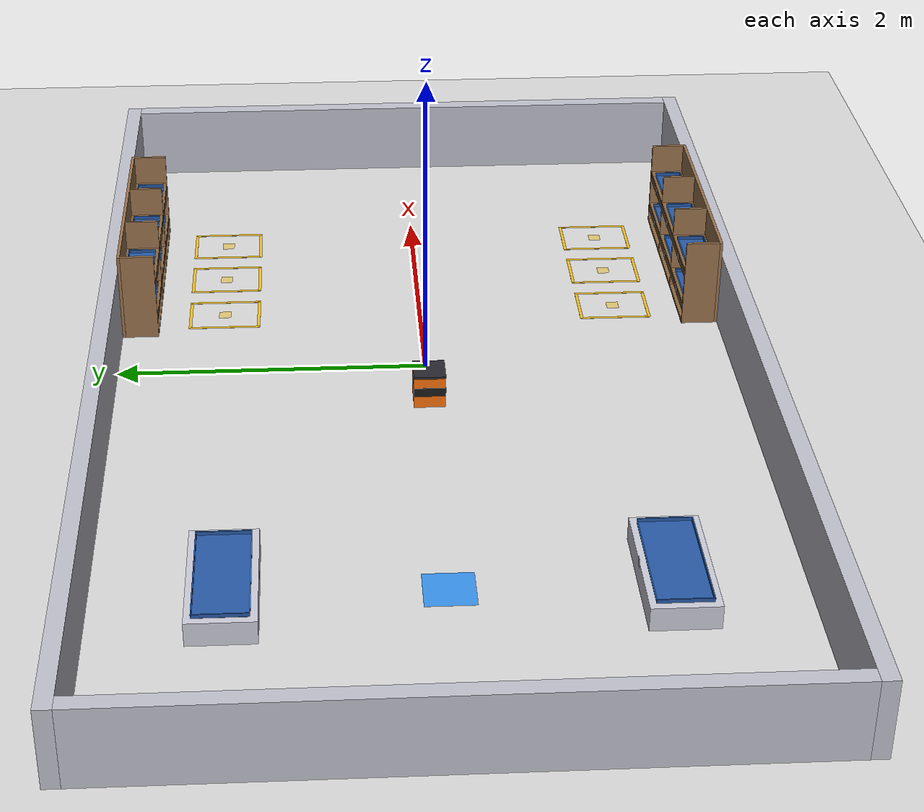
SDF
<?xml version="1.0"?>
<sdf version="1.6">
  <world name="warehouse">

    <!-- ── Vật lý ──────────────────────────────────────────────────────── -->
    <physics type="ode">
      <max_step_size>0.002</max_step_size>
      <real_time_update_rate>500</real_time_update_rate>
      <ode>
        <solver>
          <type>quick</type>
          <iters>50</iters>
          <sor>1.3</sor>
        </solver>
        <constraints>
          <cfm>0.0</cfm>
          <erp>0.2</erp>
        </constraints>
      </ode>
    </physics>

    <!-- ── Plugin trạng thái ───────────────────────────────────────────── -->
    <plugin name="gazebo_ros_state" filename="libgazebo_ros_state.so">
      <ros><namespace>/gazebo</namespace></ros>
      <update_rate>20</update_rate>
    </plugin>

    <!-- ── Ánh sáng ────────────────────────────────────────────────────── -->
    <light name="sun" type="directional">
      <cast_shadows>false</cast_shadows>
      <pose>0 0 10 0 0 0</pose>
      <diffuse>0.85 0.85 0.85 1</diffuse>
      <specular>0.1 0.1 0.1 1</specular>
      <direction>-0.5 0.1 -0.9</direction>
    </light>
    <light name="point_nw" type="point">
      <cast_shadows>false</cast_shadows>
      <pose>-1.5 1.5 3.0 0 0 0</pose>
      <diffuse>0.6 0.6 0.65 1</diffuse>
      <specular>0.05 0.05 0.05 1</specular>
      <attenuation><range>8</range><constant>0.3</constant><linear>0.05</linear><quadratic>0.0</quadratic></attenuation>
    </light>
    <light name="point_ne" type="point">
      <cast_shadows>false</cast_shadows>
      <pose>1.5 1.5 3.0 0 0 0</pose>
      <diffuse>0.6 0.6 0.65 1</diffuse>
      <specular>0.05 0.05 0.05 1</specular>
      <attenuation><range>8</range><constant>0.3</constant><linear>0.05</linear><quadratic>0.0</quadratic></attenuation>
    </light>
    <light name="point_sw" type="point">
      <cast_shadows>false</cast_shadows>
      <pose>-1.5 -1.5 3.0 0 0 0</pose>
      <diffuse>0.6 0.6 0.65 1</diffuse>
      <specular>0.05 0.05 0.05 1</specular>
      <attenuation><range>8</range><constant>0.3</constant><linear>0.05</linear><quadratic>0.0</quadratic></attenuation>
    </light>
    <light name="point_se" type="point">
      <cast_shadows>false</cast_shadows>
      <pose>1.5 -1.5 3.0 0 0 0</pose>
      <diffuse>0.6 0.6 0.65 1</diffuse>
      <specular>0.05 0.05 0.05 1</specular>
      <attenuation><range>8</range><constant>0.3</constant><linear>0.05</linear><quadratic>0.0</quadratic></attenuation>
    </light>

    <!-- ── Sàn ─────────────────────────────────────────────────────────── -->
    <model name="ground_plane">
      <static>true</static>
      <link name="link">
        <collision name="col">
          <geometry><plane><normal>0 0 1</normal><size>10.0 6.0</size></plane></geometry>
          <surface><friction><ode><mu>1.0</mu><mu2>1.0</mu2></ode></friction></surface>
        </collision>
        <visual name="vis">
          <cast_shadows>false</cast_shadows>
          <geometry><plane><normal>0 0 1</normal><size>10.0 6.0</size></plane></geometry>
          <material>
            <ambient>0.85 0.85 0.85 1</ambient>
            <diffuse>0.85 0.85 0.85 1</diffuse>
          </material>
        </visual>
      </link>
    </model>

    <!-- ── Models ──────────────────────────────────────────────────────── -->

    <model name="wall_north">
      <static>true</static>
      <pose>-0.4000 2.0500 0.2500 0.000000 0.000000 0.000000</pose>
      <link name="link">
        <collision name="col">
          <geometry><box><size>7.0 0.1 0.5</size></box></geometry>
          <surface><friction><ode><mu>1.0</mu><mu2>1.0</mu2></ode></friction></surface>
        </collision>
        <visual name="vis">
          <cast_shadows>false</cast_shadows>
          <geometry><box><size>7.0 0.1 0.5</size></box></geometry>
          <material><ambient>0.75 0.75 0.80 1.0</ambient><diffuse>0.75 0.75 0.80 1.0</diffuse></material>
        </visual>
      </link>
    </model>

    <model name="wall_south">
      <static>true</static>
      <pose>-0.4000 -2.0500 0.2500 0.000000 0.000000 0.000000</pose>
      <link name="link">
        <collision name="col">
          <geometry><box><size>7.0 0.1 0.5</size></box></geometry>
          <surface><friction><ode><mu>1.0</mu><mu2>1.0</mu2></ode></friction></surface>
        </collision>
        <visual name="vis">
          <cast_shadows>false</cast_shadows>
          <geometry><box><size>7.0 0.1 0.5</size></box></geometry>
          <material><ambient>0.75 0.75 0.80 1.0</ambient><diffuse>0.75 0.75 0.80 1.0</diffuse></material>
        </visual>
      </link>
    </model>

    <model name="wall_east">
      <static>true</static>
      <pose>3.0500 0.0000 0.2500 0.000000 0.000000 0.000000</pose>
      <link name="link">
        <collision name="col">
          <geometry><box><size>0.1 4.0 0.5</size></box></geometry>
          <surface><friction><ode><mu>1.0</mu><mu2>1.0</mu2></ode></friction></surface>
        </collision>
        <visual name="vis">
          <cast_shadows>false</cast_shadows>
          <geometry><box><size>0.1 4.0 0.5</size></box></geometry>
          <material><ambient>0.75 0.75 0.80 1.0</ambient><diffuse>0.75 0.75 0.80 1.0</diffuse></material>
        </visual>
      </link>
    </model>

    <model name="wall_west">
      <static>true</static>
      <pose>-3.8500 0.0000 0.2500 0.000000 0.000000 0.000000</pose>
      <link name="link">
        <collision name="col">
          <geometry><box><size>0.1 4.0 0.5</size></box></geometry>
          <surface><friction><ode><mu>1.0</mu><mu2>1.0</mu2></ode></friction></surface>
        </collision>
        <visual name="vis">
          <cast_shadows>false</cast_shadows>
          <geometry><box><size>0.1 4.0 0.5</size></box></geometry>
          <material><ambient>0.75 0.75 0.80 1.0</ambient><diffuse>0.75 0.75 0.80 1.0</diffuse></material>
        </visual>
      </link>
    </model>

    <model name="rack_a_back_wall">
      <static>true</static>
      <pose>1.2500 1.9900 0.3000 0.000000 0.000000 0.000000</pose>
      <link name="link">
        <collision name="col">
          <geometry><box><size>1.54 0.02 0.6</size></box></geometry>
          <surface><friction><ode><mu>0.5</mu><mu2>0.5</mu2></ode></friction></surface>
        </collision>
        <visual name="vis">
          <cast_shadows>false</cast_shadows>
          <geometry><box><size>1.54 0.02 0.6</size></box></geometry>
          <material><ambient>0.6 0.45 0.30 1.0</ambient><diffuse>0.6 0.45 0.30 1.0</diffuse></material>
        </visual>
      </link>
    </model>

    <model name="rack_a_level_1_plank">
      <static>true</static>
      <pose>1.2500 1.8700 0.1400 0.000000 0.000000 0.000000</pose>
      <link name="link">
        <collision name="col">
          <geometry><box><size>1.5 0.22 0.02</size></box></geometry>
          <surface><friction><ode><mu>0.7</mu><mu2>0.7</mu2></ode></friction></surface>
        </collision>
        <visual name="vis">
          <cast_shadows>false</cast_shadows>
          <geometry><box><size>1.5 0.22 0.02</size></box></geometry>
          <material><ambient>0.55 0.40 0.25 1.0</ambient><diffuse>0.55 0.40 0.25 1.0</diffuse></material>
        </visual>
      </link>
    </model>

    <model name="rack_a_level_2_plank">
      <static>true</static>
      <pose>1.2500 1.8700 0.3900 0.000000 0.000000 0.000000</pose>
      <link name="link">
        <collision name="col">
          <geometry><box><size>1.5 0.22 0.02</size></box></geometry>
          <surface><friction><ode><mu>0.7</mu><mu2>0.7</mu2></ode></friction></surface>
        </collision>
        <visual name="vis">
          <cast_shadows>false</cast_shadows>
          <geometry><box><size>1.5 0.22 0.02</size></box></geometry>
          <material><ambient>0.55 0.40 0.25 1.0</ambient><diffuse>0.55 0.40 0.25 1.0</diffuse></material>
        </visual>
      </link>
    </model>

    <model name="rack_a_floor_plank">
      <static>true</static>
      <pose>1.2500 1.8700 0.0050 0.000000 0.000000 0.000000</pose>
      <link name="link">
        <collision name="col">
          <geometry><box><size>1.5 0.22 0.02</size></box></geometry>
          <surface><friction><ode><mu>0.7</mu><mu2>0.7</mu2></ode></friction></surface>
        </collision>
        <visual name="vis">
          <cast_shadows>false</cast_shadows>
          <geometry><box><size>1.5 0.22 0.02</size></box></geometry>
          <material><ambient>0.55 0.40 0.25 1.0</ambient><diffuse>0.55 0.40 0.25 1.0</diffuse></material>
        </visual>
      </link>
    </model>

    <model name="rack_a_left_side">
      <static>true</static>
      <pose>0.4900 1.8700 0.3000 0.000000 0.000000 0.000000</pose>
      <link name="link">
        <collision name="col">
          <geometry><box><size>0.02 0.22 0.6</size></box></geometry>
          <surface><friction><ode><mu>0.5</mu><mu2>0.5</mu2></ode></friction></surface>
        </collision>
        <visual name="vis">
          <cast_shadows>false</cast_shadows>
          <geometry><box><size>0.02 0.22 0.6</size></box></geometry>
          <material><ambient>0.6 0.45 0.30 1.0</ambient><diffuse>0.6 0.45 0.30 1.0</diffuse></material>
        </visual>
      </link>
    </model>

    <model name="rack_a_right_side">
      <static>true</static>
      <pose>2.0100 1.8700 0.3000 0.000000 0.000000 0.000000</pose>
      <link name="link">
        <collision name="col">
          <geometry><box><size>0.02 0.22 0.6</size></box></geometry>
          <surface><friction><ode><mu>0.5</mu><mu2>0.5</mu2></ode></friction></surface>
        </collision>
        <visual name="vis">
          <cast_shadows>false</cast_shadows>
          <geometry><box><size>0.02 0.22 0.6</size></box></geometry>
          <material><ambient>0.6 0.45 0.30 1.0</ambient><diffuse>0.6 0.45 0.30 1.0</diffuse></material>
        </visual>
      </link>
    </model>

    <model name="rack_a_divider_0">
      <static>true</static>
      <pose>1.0000 1.8700 0.3000 0.000000 0.000000 0.000000</pose>
      <link name="link">
        <collision name="col">
          <geometry><box><size>0.015 0.22 0.6</size></box></geometry>
          <surface><friction><ode><mu>0.5</mu><mu2>0.5</mu2></ode></friction></surface>
        </collision>
        <visual name="vis">
          <cast_shadows>false</cast_shadows>
          <geometry><box><size>0.015 0.22 0.6</size></box></geometry>
          <material><ambient>0.6 0.45 0.30 1.0</ambient><diffuse>0.6 0.45 0.30 1.0</diffuse></material>
        </visual>
      </link>
    </model>

    <model name="rack_a_divider_1">
      <static>true</static>
      <pose>1.5000 1.8700 0.3000 0.000000 0.000000 0.000000</pose>
      <link name="link">
        <collision name="col">
          <geometry><box><size>0.015 0.22 0.6</size></box></geometry>
          <surface><friction><ode><mu>0.5</mu><mu2>0.5</mu2></ode></friction></surface>
        </collision>
        <visual name="vis">
          <cast_shadows>false</cast_shadows>
          <geometry><box><size>0.015 0.22 0.6</size></box></geometry>
          <material><ambient>0.6 0.45 0.30 1.0</ambient><diffuse>0.6 0.45 0.30 1.0</diffuse></material>
        </visual>
      </link>
    </model>

    <model name="rack_a_level_1_front_beam">
      <static>true</static>
      <pose>1.2500 1.7650 0.1100 0.000000 0.000000 0.000000</pose>
      <link name="link">

        <visual name="vis">
          <cast_shadows>false</cast_shadows>
          <geometry><box><size>1.5 0.01 0.04</size></box></geometry>
          <material><ambient>0.50 0.38 0.24 1.0</ambient><diffuse>0.50 0.38 0.24 1.0</diffuse></material>
        </visual>
      </link>
    </model>

    <model name="rack_a_level_2_front_beam">
      <static>true</static>
      <pose>1.2500 1.7650 0.3600 0.000000 0.000000 0.000000</pose>
      <link name="link">

        <visual name="vis">
          <cast_shadows>false</cast_shadows>
          <geometry><box><size>1.5 0.01 0.04</size></box></geometry>
          <material><ambient>0.50 0.38 0.24 1.0</ambient><diffuse>0.50 0.38 0.24 1.0</diffuse></material>
        </visual>
      </link>
    </model>

    <model name="tag_slot_0">
      <static>true</static>
      <pose>0.7500 1.7590 0.1100 0.000000 0.000000 3.141593</pose>
      <link name="link">
        <collision name="col">
          <geometry><box><size>0.05 0.001 0.05</size></box></geometry>
        </collision>
        <visual name="vis">
          <cast_shadows>false</cast_shadows>
          <geometry><box><size>0.05 0.001 0.05</size></box></geometry>
          <material>
            <script>
              <uri>model://aruco_tags/materials/scripts</uri>
              <uri>model://aruco_tags/materials/textures</uri>
              <name>Aruco/Tag0</name>
            </script>
          </material>
        </visual>
      </link>
    </model>

    <model name="tag_slot_1">
      <static>true</static>
      <pose>1.2500 1.7590 0.1100 0.000000 0.000000 3.141593</pose>
      <link name="link">
        <collision name="col">
          <geometry><box><size>0.05 0.001 0.05</size></box></geometry>
        </collision>
        <visual name="vis">
          <cast_shadows>false</cast_shadows>
          <geometry><box><size>0.05 0.001 0.05</size></box></geometry>
          <material>
            <script>
              <uri>model://aruco_tags/materials/scripts</uri>
              <uri>model://aruco_tags/materials/textures</uri>
              <name>Aruco/Tag1</name>
            </script>
          </material>
        </visual>
      </link>
    </model>

    <model name="tag_slot_2">
      <static>true</static>
      <pose>1.7500 1.7590 0.1100 0.000000 0.000000 3.141593</pose>
      <link name="link">
        <collision name="col">
          <geometry><box><size>0.05 0.001 0.05</size></box></geometry>
        </collision>
        <visual name="vis">
          <cast_shadows>false</cast_shadows>
          <geometry><box><size>0.05 0.001 0.05</size></box></geometry>
          <material>
            <script>
              <uri>model://aruco_tags/materials/scripts</uri>
              <uri>model://aruco_tags/materials/textures</uri>
              <name>Aruco/Tag2</name>
            </script>
          </material>
        </visual>
      </link>
    </model>

    <model name="tag_slot_3">
      <static>true</static>
      <pose>0.7500 1.7590 0.3600 0.000000 0.000000 3.141593</pose>
      <link name="link">
        <collision name="col">
          <geometry><box><size>0.05 0.001 0.05</size></box></geometry>
        </collision>
        <visual name="vis">
          <cast_shadows>false</cast_shadows>
          <geometry><box><size>0.05 0.001 0.05</size></box></geometry>
          <material>
            <script>
              <uri>model://aruco_tags/materials/scripts</uri>
              <uri>model://aruco_tags/materials/textures</uri>
              <name>Aruco/Tag3</name>
            </script>
          </material>
        </visual>
      </link>
    </model>

    <model name="tag_slot_4">
      <static>true</static>
      <pose>1.2500 1.7590 0.3600 0.000000 0.000000 3.141593</pose>
      <link name="link">
        <collision name="col">
          <geometry><box><size>0.05 0.001 0.05</size></box></geometry>
        </collision>
        <visual name="vis">
          <cast_shadows>false</cast_shadows>
          <geometry><box><size>0.05 0.001 0.05</size></box></geometry>
          <material>
            <script>
              <uri>model://aruco_tags/materials/scripts</uri>
              <uri>model://aruco_tags/materials/textures</uri>
              <name>Aruco/Tag4</name>
            </script>
          </material>
        </visual>
      </link>
    </model>

    <model name="tag_slot_5">
      <static>true</static>
      <pose>1.7500 1.7590 0.3600 0.000000 0.000000 3.141593</pose>
      <link name="link">
        <collision name="col">
          <geometry><box><size>0.05 0.001 0.05</size></box></geometry>
        </collision>
        <visual name="vis">
          <cast_shadows>false</cast_shadows>
          <geometry><box><size>0.05 0.001 0.05</size></box></geometry>
          <material>
            <script>
              <uri>model://aruco_tags/materials/scripts</uri>
              <uri>model://aruco_tags/materials/textures</uri>
              <name>Aruco/Tag5</name>
            </script>
          </material>
        </visual>
      </link>
    </model>

    <model name="shelf_tray_0">
      <static>true</static>
      <pose>0.7500 1.8700 0.1500 0.000000 0.000000 0.000000</pose>
      <link name="link">
        <!-- Đáy khay mỏng 2mm sát mặt sàn -->
        <visual name="bottom_vis">
          <pose>0 0 0.001 0 0 0</pose>
          <geometry><box><size>0.36 0.18 0.002</size></box></geometry>
          <material><ambient>0.15 0.35 0.65 1.0</ambient><diffuse>0.15 0.35 0.65 1.0</diffuse></material>
        </visual>
        <!-- Thành sau khay -->
        <visual name="back_wall_vis">
          <pose>0 0.087 0.012 0 0 0</pose>
          <geometry><box><size>0.36 0.006 0.024</size></box></geometry>
          <material><ambient>0.15 0.35 0.65 1.0</ambient><diffuse>0.15 0.35 0.65 1.0</diffuse></material>
        </visual>
        <!-- Thành trái khay -->
        <visual name="left_wall_vis">
          <pose>-0.177 0 0.012 0 0 0</pose>
          <geometry><box><size>0.006 0.18 0.024</size></box></geometry>
          <material><ambient>0.15 0.35 0.65 1.0</ambient><diffuse>0.15 0.35 0.65 1.0</diffuse></material>
        </visual>
        <!-- Thành phải khay -->
        <visual name="right_wall_vis">
          <pose>0.177 0 0.012 0 0 0</pose>
          <geometry><box><size>0.006 0.18 0.024</size></box></geometry>
          <material><ambient>0.15 0.35 0.65 1.0</ambient><diffuse>0.15 0.35 0.65 1.0</diffuse></material>
        </visual>
        <!-- Gờ mép trước thấp 4mm -->
        <visual name="front_lip_vis">
          <pose>0 -0.087 0.004 0 0 0</pose>
          <geometry><box><size>0.36 0.006 0.008</size></box></geometry>
          <material><ambient>0.20 0.50 0.85 1.0</ambient><diffuse>0.20 0.50 0.85 1.0</diffuse></material>
        </visual>
        <!-- Collisions thành khay bảo vệ hộp -->
        <collision name="back_col">
          <pose>0 0.087 0.012 0 0 0</pose>
          <geometry><box><size>0.36 0.006 0.024</size></box></geometry>
        </collision>
        <collision name="left_col">
          <pose>-0.177 0 0.012 0 0 0</pose>
          <geometry><box><size>0.006 0.18 0.024</size></box></geometry>
        </collision>
        <collision name="right_col">
          <pose>0.177 0 0.012 0 0 0</pose>
          <geometry><box><size>0.006 0.18 0.024</size></box></geometry>
        </collision>
      </link>
    </model>

    <model name="shelf_tray_1">
      <static>true</static>
      <pose>1.2500 1.8700 0.1500 0.000000 0.000000 0.000000</pose>
      <link name="link">
        <!-- Đáy khay mỏng 2mm sát mặt sàn -->
        <visual name="bottom_vis">
          <pose>0 0 0.001 0 0 0</pose>
          <geometry><box><size>0.36 0.18 0.002</size></box></geometry>
          <material><ambient>0.15 0.35 0.65 1.0</ambient><diffuse>0.15 0.35 0.65 1.0</diffuse></material>
        </visual>
        <!-- Thành sau khay -->
        <visual name="back_wall_vis">
          <pose>0 0.087 0.012 0 0 0</pose>
          <geometry><box><size>0.36 0.006 0.024</size></box></geometry>
          <material><ambient>0.15 0.35 0.65 1.0</ambient><diffuse>0.15 0.35 0.65 1.0</diffuse></material>
        </visual>
        <!-- Thành trái khay -->
        <visual name="left_wall_vis">
          <pose>-0.177 0 0.012 0 0 0</pose>
          <geometry><box><size>0.006 0.18 0.024</size></box></geometry>
          <material><ambient>0.15 0.35 0.65 1.0</ambient><diffuse>0.15 0.35 0.65 1.0</diffuse></material>
        </visual>
        <!-- Thành phải khay -->
        <visual name="right_wall_vis">
          <pose>0.177 0 0.012 0 0 0</pose>
          <geometry><box><size>0.006 0.18 0.024</size></box></geometry>
          <material><ambient>0.15 0.35 0.65 1.0</ambient><diffuse>0.15 0.35 0.65 1.0</diffuse></material>
        </visual>
        <!-- Gờ mép trước thấp 4mm -->
        <visual name="front_lip_vis">
          <pose>0 -0.087 0.004 0 0 0</pose>
          <geometry><box><size>0.36 0.006 0.008</size></box></geometry>
          <material><ambient>0.20 0.50 0.85 1.0</ambient><diffuse>0.20 0.50 0.85 1.0</diffuse></material>
        </visual>
        <!-- Collisions thành khay bảo vệ hộp -->
        <collision name="back_col">
          <pose>0 0.087 0.012 0 0 0</pose>
          <geometry><box><size>0.36 0.006 0.024</size></box></geometry>
        </collision>
        <collision name="left_col">
          <pose>-0.177 0 0.012 0 0 0</pose>
          <geometry><box><size>0.006 0.18 0.024</size></box></geometry>
        </collision>
        <collision name="right_col">
          <pose>0.177 0 0.012 0 0 0</pose>
          <geometry><box><size>0.006 0.18 0.024</size></box></geometry>
        </collision>
      </link>
    </model>

    <model name="shelf_tray_2">
      <static>true</static>
      <pose>1.7500 1.8700 0.1500 0.000000 0.000000 0.000000</pose>
      <link name="link">
        <!-- Đáy khay mỏng 2mm sát mặt sàn -->
        <visual name="bottom_vis">
          <pose>0 0 0.001 0 0 0</pose>
          <geometry><box><size>0.36 0.18 0.002</size></box></geometry>
          <material><ambient>0.15 0.35 0.65 1.0</ambient><diffuse>0.15 0.35 0.65 1.0</diffuse></material>
        </visual>
        <!-- Thành sau khay -->
        <visual name="back_wall_vis">
          <pose>0 0.087 0.012 0 0 0</pose>
          <geometry><box><size>0.36 0.006 0.024</size></box></geometry>
          <material><ambient>0.15 0.35 0.65 1.0</ambient><diffuse>0.15 0.35 0.65 1.0</diffuse></material>
        </visual>
        <!-- Thành trái khay -->
        <visual name="left_wall_vis">
          <pose>-0.177 0 0.012 0 0 0</pose>
          <geometry><box><size>0.006 0.18 0.024</size></box></geometry>
          <material><ambient>0.15 0.35 0.65 1.0</ambient><diffuse>0.15 0.35 0.65 1.0</diffuse></material>
        </visual>
        <!-- Thành phải khay -->
        <visual name="right_wall_vis">
          <pose>0.177 0 0.012 0 0 0</pose>
          <geometry><box><size>0.006 0.18 0.024</size></box></geometry>
          <material><ambient>0.15 0.35 0.65 1.0</ambient><diffuse>0.15 0.35 0.65 1.0</diffuse></material>
        </visual>
        <!-- Gờ mép trước thấp 4mm -->
        <visual name="front_lip_vis">
          <pose>0 -0.087 0.004 0 0 0</pose>
          <geometry><box><size>0.36 0.006 0.008</size></box></geometry>
          <material><ambient>0.20 0.50 0.85 1.0</ambient><diffuse>0.20 0.50 0.85 1.0</diffuse></material>
        </visual>
        <!-- Collisions thành khay bảo vệ hộp -->
        <collision name="back_col">
          <pose>0 0.087 0.012 0 0 0</pose>
          <geometry><box><size>0.36 0.006 0.024</size></box></geometry>
        </collision>
        <collision name="left_col">
          <pose>-0.177 0 0.012 0 0 0</pose>
          <geometry><box><size>0.006 0.18 0.024</size></box></geometry>
        </collision>
        <collision name="right_col">
          <pose>0.177 0 0.012 0 0 0</pose>
          <geometry><box><size>0.006 0.18 0.024</size></box></geometry>
        </collision>
      </link>
    </model>

    <model name="shelf_tray_3">
      <static>true</static>
      <pose>0.7500 1.8700 0.4000 0.000000 0.000000 0.000000</pose>
      <link name="link">
        <!-- Đáy khay mỏng 2mm sát mặt sàn -->
        <visual name="bottom_vis">
          <pose>0 0 0.001 0 0 0</pose>
          <geometry><box><size>0.36 0.18 0.002</size></box></geometry>
          <material><ambient>0.15 0.35 0.65 1.0</ambient><diffuse>0.15 0.35 0.65 1.0</diffuse></material>
        </visual>
        <!-- Thành sau khay -->
        <visual name="back_wall_vis">
          <pose>0 0.087 0.012 0 0 0</pose>
          <geometry><box><size>0.36 0.006 0.024</size></box></geometry>
          <material><ambient>0.15 0.35 0.65 1.0</ambient><diffuse>0.15 0.35 0.65 1.0</diffuse></material>
        </visual>
        <!-- Thành trái khay -->
        <visual name="left_wall_vis">
          <pose>-0.177 0 0.012 0 0 0</pose>
          <geometry><box><size>0.006 0.18 0.024</size></box></geometry>
          <material><ambient>0.15 0.35 0.65 1.0</ambient><diffuse>0.15 0.35 0.65 1.0</diffuse></material>
        </visual>
        <!-- Thành phải khay -->
        <visual name="right_wall_vis">
          <pose>0.177 0 0.012 0 0 0</pose>
          <geometry><box><size>0.006 0.18 0.024</size></box></geometry>
          <material><ambient>0.15 0.35 0.65 1.0</ambient><diffuse>0.15 0.35 0.65 1.0</diffuse></material>
        </visual>
        <!-- Gờ mép trước thấp 4mm -->
        <visual name="front_lip_vis">
          <pose>0 -0.087 0.004 0 0 0</pose>
          <geometry><box><size>0.36 0.006 0.008</size></box></geometry>
          <material><ambient>0.20 0.50 0.85 1.0</ambient><diffuse>0.20 0.50 0.85 1.0</diffuse></material>
        </visual>
        <!-- Collisions thành khay bảo vệ hộp -->
        <collision name="back_col">
          <pose>0 0.087 0.012 0 0 0</pose>
          <geometry><box><size>0.36 0.006 0.024</size></box></geometry>
        </collision>
        <collision name="left_col">
          <pose>-0.177 0 0.012 0 0 0</pose>
          <geometry><box><size>0.006 0.18 0.024</size></box></geometry>
        </collision>
        <collision name="right_col">
          <pose>0.177 0 0.012 0 0 0</pose>
          <geometry><box><size>0.006 0.18 0.024</size></box></geometry>
        </collision>
      </link>
    </model>

    <model name="shelf_tray_4">
      <static>true</static>
      <pose>1.2500 1.8700 0.4000 0.000000 0.000000 0.000000</pose>
      <link name="link">
        <!-- Đáy khay mỏng 2mm sát mặt sàn -->
        <visual name="bottom_vis">
          <pose>0 0 0.001 0 0 0</pose>
          <geometry><box><size>0.36 0.18 0.002</size></box></geometry>
          <material><ambient>0.15 0.35 0.65 1.0</ambient><diffuse>0.15 0.35 0.65 1.0</diffuse></material>
        </visual>
        <!-- Thành sau khay -->
        <visual name="back_wall_vis">
          <pose>0 0.087 0.012 0 0 0</pose>
          <geometry><box><size>0.36 0.006 0.024</size></box></geometry>
          <material><ambient>0.15 0.35 0.65 1.0</ambient><diffuse>0.15 0.35 0.65 1.0</diffuse></material>
        </visual>
        <!-- Thành trái khay -->
        <visual name="left_wall_vis">
          <pose>-0.177 0 0.012 0 0 0</pose>
          <geometry><box><size>0.006 0.18 0.024</size></box></geometry>
          <material><ambient>0.15 0.35 0.65 1.0</ambient><diffuse>0.15 0.35 0.65 1.0</diffuse></material>
        </visual>
        <!-- Thành phải khay -->
        <visual name="right_wall_vis">
          <pose>0.177 0 0.012 0 0 0</pose>
          <geometry><box><size>0.006 0.18 0.024</size></box></geometry>
          <material><ambient>0.15 0.35 0.65 1.0</ambient><diffuse>0.15 0.35 0.65 1.0</diffuse></material>
        </visual>
        <!-- Gờ mép trước thấp 4mm -->
        <visual name="front_lip_vis">
          <pose>0 -0.087 0.004 0 0 0</pose>
          <geometry><box><size>0.36 0.006 0.008</size></box></geometry>
          <material><ambient>0.20 0.50 0.85 1.0</ambient><diffuse>0.20 0.50 0.85 1.0</diffuse></material>
        </visual>
        <!-- Collisions thành khay bảo vệ hộp -->
        <collision name="back_col">
          <pose>0 0.087 0.012 0 0 0</pose>
          <geometry><box><size>0.36 0.006 0.024</size></box></geometry>
        </collision>
        <collision name="left_col">
          <pose>-0.177 0 0.012 0 0 0</pose>
          <geometry><box><size>0.006 0.18 0.024</size></box></geometry>
        </collision>
        <collision name="right_col">
          <pose>0.177 0 0.012 0 0 0</pose>
          <geometry><box><size>0.006 0.18 0.024</size></box></geometry>
        </collision>
      </link>
    </model>

    <model name="shelf_tray_5">
      <static>true</static>
      <pose>1.7500 1.8700 0.4000 0.000000 0.000000 0.000000</pose>
      <link name="link">
        <!-- Đáy khay mỏng 2mm sát mặt sàn -->
        <visual name="bottom_vis">
          <pose>0 0 0.001 0 0 0</pose>
          <geometry><box><size>0.36 0.18 0.002</size></box></geometry>
          <material><ambient>0.15 0.35 0.65 1.0</ambient><diffuse>0.15 0.35 0.65 1.0</diffuse></material>
        </visual>
        <!-- Thành sau khay -->
        <visual name="back_wall_vis">
          <pose>0 0.087 0.012 0 0 0</pose>
          <geometry><box><size>0.36 0.006 0.024</size></box></geometry>
          <material><ambient>0.15 0.35 0.65 1.0</ambient><diffuse>0.15 0.35 0.65 1.0</diffuse></material>
        </visual>
        <!-- Thành trái khay -->
        <visual name="left_wall_vis">
          <pose>-0.177 0 0.012 0 0 0</pose>
          <geometry><box><size>0.006 0.18 0.024</size></box></geometry>
          <material><ambient>0.15 0.35 0.65 1.0</ambient><diffuse>0.15 0.35 0.65 1.0</diffuse></material>
        </visual>
        <!-- Thành phải khay -->
        <visual name="right_wall_vis">
          <pose>0.177 0 0.012 0 0 0</pose>
          <geometry><box><size>0.006 0.18 0.024</size></box></geometry>
          <material><ambient>0.15 0.35 0.65 1.0</ambient><diffuse>0.15 0.35 0.65 1.0</diffuse></material>
        </visual>
        <!-- Gờ mép trước thấp 4mm -->
        <visual name="front_lip_vis">
          <pose>0 -0.087 0.004 0 0 0</pose>
          <geometry><box><size>0.36 0.006 0.008</size></box></geometry>
          <material><ambient>0.20 0.50 0.85 1.0</ambient><diffuse>0.20 0.50 0.85 1.0</diffuse></material>
        </visual>
        <!-- Collisions thành khay bảo vệ hộp -->
        <collision name="back_col">
          <pose>0 0.087 0.012 0 0 0</pose>
          <geometry><box><size>0.36 0.006 0.024</size></box></geometry>
        </collision>
        <collision name="left_col">
          <pose>-0.177 0 0.012 0 0 0</pose>
          <geometry><box><size>0.006 0.18 0.024</size></box></geometry>
        </collision>
        <collision name="right_col">
          <pose>0.177 0 0.012 0 0 0</pose>
          <geometry><box><size>0.006 0.18 0.024</size></box></geometry>
        </collision>
      </link>
    </model>

    <model name="rack_b_back_wall">
      <static>true</static>
      <pose>1.2500 -1.9900 0.3000 0.000000 0.000000 0.000000</pose>
      <link name="link">
        <collision name="col">
          <geometry><box><size>1.54 0.02 0.6</size></box></geometry>
          <surface><friction><ode><mu>0.5</mu><mu2>0.5</mu2></ode></friction></surface>
        </collision>
        <visual name="vis">
          <cast_shadows>false</cast_shadows>
          <geometry><box><size>1.54 0.02 0.6</size></box></geometry>
          <material><ambient>0.6 0.45 0.30 1.0</ambient><diffuse>0.6 0.45 0.30 1.0</diffuse></material>
        </visual>
      </link>
    </model>

    <model name="rack_b_level_1_plank">
      <static>true</static>
      <pose>1.2500 -1.8700 0.1400 0.000000 0.000000 0.000000</pose>
      <link name="link">
        <collision name="col">
          <geometry><box><size>1.5 0.22 0.02</size></box></geometry>
          <surface><friction><ode><mu>0.7</mu><mu2>0.7</mu2></ode></friction></surface>
        </collision>
        <visual name="vis">
          <cast_shadows>false</cast_shadows>
          <geometry><box><size>1.5 0.22 0.02</size></box></geometry>
          <material><ambient>0.55 0.40 0.25 1.0</ambient><diffuse>0.55 0.40 0.25 1.0</diffuse></material>
        </visual>
      </link>
    </model>

    <model name="rack_b_level_2_plank">
      <static>true</static>
      <pose>1.2500 -1.8700 0.3900 0.000000 0.000000 0.000000</pose>
      <link name="link">
        <collision name="col">
          <geometry><box><size>1.5 0.22 0.02</size></box></geometry>
          <surface><friction><ode><mu>0.7</mu><mu2>0.7</mu2></ode></friction></surface>
        </collision>
        <visual name="vis">
          <cast_shadows>false</cast_shadows>
          <geometry><box><size>1.5 0.22 0.02</size></box></geometry>
          <material><ambient>0.55 0.40 0.25 1.0</ambient><diffuse>0.55 0.40 0.25 1.0</diffuse></material>
        </visual>
      </link>
    </model>

    <model name="rack_b_floor_plank">
      <static>true</static>
      <pose>1.2500 -1.8700 0.0050 0.000000 0.000000 0.000000</pose>
      <link name="link">
        <collision name="col">
          <geometry><box><size>1.5 0.22 0.02</size></box></geometry>
          <surface><friction><ode><mu>0.7</mu><mu2>0.7</mu2></ode></friction></surface>
        </collision>
        <visual name="vis">
          <cast_shadows>false</cast_shadows>
          <geometry><box><size>1.5 0.22 0.02</size></box></geometry>
          <material><ambient>0.55 0.40 0.25 1.0</ambient><diffuse>0.55 0.40 0.25 1.0</diffuse></material>
        </visual>
      </link>
    </model>

    <model name="rack_b_left_side">
      <static>true</static>
      <pose>0.4900 -1.8700 0.3000 0.000000 0.000000 0.000000</pose>
      <link name="link">
        <collision name="col">
          <geometry><box><size>0.02 0.22 0.6</size></box></geometry>
          <surface><friction><ode><mu>0.5</mu><mu2>0.5</mu2></ode></friction></surface>
        </collision>
        <visual name="vis">
          <cast_shadows>false</cast_shadows>
          <geometry><box><size>0.02 0.22 0.6</size></box></geometry>
          <material><ambient>0.6 0.45 0.30 1.0</ambient><diffuse>0.6 0.45 0.30 1.0</diffuse></material>
        </visual>
      </link>
    </model>

    <model name="rack_b_right_side">
      <static>true</static>
      <pose>2.0100 -1.8700 0.3000 0.000000 0.000000 0.000000</pose>
      <link name="link">
        <collision name="col">
          <geometry><box><size>0.02 0.22 0.6</size></box></geometry>
          <surface><friction><ode><mu>0.5</mu><mu2>0.5</mu2></ode></friction></surface>
        </collision>
        <visual name="vis">
          <cast_shadows>false</cast_shadows>
          <geometry><box><size>0.02 0.22 0.6</size></box></geometry>
          <material><ambient>0.6 0.45 0.30 1.0</ambient><diffuse>0.6 0.45 0.30 1.0</diffuse></material>
        </visual>
      </link>
    </model>

    <model name="rack_b_divider_0">
      <static>true</static>
      <pose>1.0000 -1.8700 0.3000 0.000000 0.000000 0.000000</pose>
      <link name="link">
        <collision name="col">
          <geometry><box><size>0.015 0.22 0.6</size></box></geometry>
          <surface><friction><ode><mu>0.5</mu><mu2>0.5</mu2></ode></friction></surface>
        </collision>
        <visual name="vis">
          <cast_shadows>false</cast_shadows>
          <geometry><box><size>0.015 0.22 0.6</size></box></geometry>
          <material><ambient>0.6 0.45 0.30 1.0</ambient><diffuse>0.6 0.45 0.30 1.0</diffuse></material>
        </visual>
      </link>
    </model>

    <model name="rack_b_divider_1">
      <static>true</static>
      <pose>1.5000 -1.8700 0.3000 0.000000 0.000000 0.000000</pose>
      <link name="link">
        <collision name="col">
          <geometry><box><size>0.015 0.22 0.6</size></box></geometry>
          <surface><friction><ode><mu>0.5</mu><mu2>0.5</mu2></ode></friction></surface>
        </collision>
        <visual name="vis">
          <cast_shadows>false</cast_shadows>
          <geometry><box><size>0.015 0.22 0.6</size></box></geometry>
          <material><ambient>0.6 0.45 0.30 1.0</ambient><diffuse>0.6 0.45 0.30 1.0</diffuse></material>
        </visual>
      </link>
    </model>

    <model name="rack_b_level_1_front_beam">
      <static>true</static>
      <pose>1.2500 -1.7650 0.1100 0.000000 0.000000 0.000000</pose>
      <link name="link">

        <visual name="vis">
          <cast_shadows>false</cast_shadows>
          <geometry><box><size>1.5 0.01 0.04</size></box></geometry>
          <material><ambient>0.50 0.38 0.24 1.0</ambient><diffuse>0.50 0.38 0.24 1.0</diffuse></material>
        </visual>
      </link>
    </model>

    <model name="rack_b_level_2_front_beam">
      <static>true</static>
      <pose>1.2500 -1.7650 0.3600 0.000000 0.000000 0.000000</pose>
      <link name="link">

        <visual name="vis">
          <cast_shadows>false</cast_shadows>
          <geometry><box><size>1.5 0.01 0.04</size></box></geometry>
          <material><ambient>0.50 0.38 0.24 1.0</ambient><diffuse>0.50 0.38 0.24 1.0</diffuse></material>
        </visual>
      </link>
    </model>

    <model name="tag_slot_6">
      <static>true</static>
      <pose>0.7500 -1.7590 0.1100 0.000000 0.000000 0.000000</pose>
      <link name="link">
        <collision name="col">
          <geometry><box><size>0.05 0.001 0.05</size></box></geometry>
        </collision>
        <visual name="vis">
          <cast_shadows>false</cast_shadows>
          <geometry><box><size>0.05 0.001 0.05</size></box></geometry>
          <material>
            <script>
              <uri>model://aruco_tags/materials/scripts</uri>
              <uri>model://aruco_tags/materials/textures</uri>
              <name>Aruco/Tag6</name>
            </script>
          </material>
        </visual>
      </link>
    </model>

    <model name="tag_slot_7">
      <static>true</static>
      <pose>1.2500 -1.7590 0.1100 0.000000 0.000000 0.000000</pose>
      <link name="link">
        <collision name="col">
          <geometry><box><size>0.05 0.001 0.05</size></box></geometry>
        </collision>
        <visual name="vis">
          <cast_shadows>false</cast_shadows>
          <geometry><box><size>0.05 0.001 0.05</size></box></geometry>
          <material>
            <script>
              <uri>model://aruco_tags/materials/scripts</uri>
              <uri>model://aruco_tags/materials/textures</uri>
              <name>Aruco/Tag7</name>
            </script>
          </material>
        </visual>
      </link>
    </model>

    <model name="tag_slot_8">
      <static>true</static>
      <pose>1.7500 -1.7590 0.1100 0.000000 0.000000 0.000000</pose>
      <link name="link">
        <collision name="col">
          <geometry><box><size>0.05 0.001 0.05</size></box></geometry>
        </collision>
        <visual name="vis">
          <cast_shadows>false</cast_shadows>
          <geometry><box><size>0.05 0.001 0.05</size></box></geometry>
          <material>
            <script>
              <uri>model://aruco_tags/materials/scripts</uri>
              <uri>model://aruco_tags/materials/textures</uri>
              <name>Aruco/Tag8</name>
            </script>
          </material>
        </visual>
      </link>
    </model>

    <model name="tag_slot_9">
      <static>true</static>
      <pose>0.7500 -1.7590 0.3600 0.000000 0.000000 0.000000</pose>
      <link name="link">
        <collision name="col">
          <geometry><box><size>0.05 0.001 0.05</size></box></geometry>
        </collision>
        <visual name="vis">
          <cast_shadows>false</cast_shadows>
          <geometry><box><size>0.05 0.001 0.05</size></box></geometry>
          <material>
            <script>
              <uri>model://aruco_tags/materials/scripts</uri>
              <uri>model://aruco_tags/materials/textures</uri>
              <name>Aruco/Tag9</name>
            </script>
          </material>
        </visual>
      </link>
    </model>

    <model name="tag_slot_10">
      <static>true</static>
      <pose>1.2500 -1.7590 0.3600 0.000000 0.000000 0.000000</pose>
      <link name="link">
        <collision name="col">
          <geometry><box><size>0.05 0.001 0.05</size></box></geometry>
        </collision>
        <visual name="vis">
          <cast_shadows>false</cast_shadows>
          <geometry><box><size>0.05 0.001 0.05</size></box></geometry>
          <material>
            <script>
              <uri>model://aruco_tags/materials/scripts</uri>
              <uri>model://aruco_tags/materials/textures</uri>
              <name>Aruco/Tag10</name>
            </script>
          </material>
        </visual>
      </link>
    </model>

    <model name="tag_slot_11">
      <static>true</static>
      <pose>1.7500 -1.7590 0.3600 0.000000 0.000000 0.000000</pose>
      <link name="link">
        <collision name="col">
          <geometry><box><size>0.05 0.001 0.05</size></box></geometry>
        </collision>
        <visual name="vis">
          <cast_shadows>false</cast_shadows>
          <geometry><box><size>0.05 0.001 0.05</size></box></geometry>
          <material>
            <script>
              <uri>model://aruco_tags/materials/scripts</uri>
              <uri>model://aruco_tags/materials/textures</uri>
              <name>Aruco/Tag11</name>
            </script>
          </material>
        </visual>
      </link>
    </model>

    <model name="shelf_tray_6">
      <static>true</static>
      <pose>0.7500 -1.8700 0.1500 0.000000 0.000000 0.000000</pose>
      <link name="link">
        <!-- Đáy khay mỏng 2mm sát mặt sàn -->
        <visual name="bottom_vis">
          <pose>0 0 0.001 0 0 0</pose>
          <geometry><box><size>0.36 0.18 0.002</size></box></geometry>
          <material><ambient>0.15 0.35 0.65 1.0</ambient><diffuse>0.15 0.35 0.65 1.0</diffuse></material>
        </visual>
        <!-- Thành sau khay -->
        <visual name="back_wall_vis">
          <pose>0 -0.087 0.012 0 0 0</pose>
          <geometry><box><size>0.36 0.006 0.024</size></box></geometry>
          <material><ambient>0.15 0.35 0.65 1.0</ambient><diffuse>0.15 0.35 0.65 1.0</diffuse></material>
        </visual>
        <!-- Thành trái khay -->
        <visual name="left_wall_vis">
          <pose>-0.177 0 0.012 0 0 0</pose>
          <geometry><box><size>0.006 0.18 0.024</size></box></geometry>
          <material><ambient>0.15 0.35 0.65 1.0</ambient><diffuse>0.15 0.35 0.65 1.0</diffuse></material>
        </visual>
        <!-- Thành phải khay -->
        <visual name="right_wall_vis">
          <pose>0.177 0 0.012 0 0 0</pose>
          <geometry><box><size>0.006 0.18 0.024</size></box></geometry>
          <material><ambient>0.15 0.35 0.65 1.0</ambient><diffuse>0.15 0.35 0.65 1.0</diffuse></material>
        </visual>
        <!-- Gờ mép trước thấp 4mm -->
        <visual name="front_lip_vis">
          <pose>0 0.087 0.004 0 0 0</pose>
          <geometry><box><size>0.36 0.006 0.008</size></box></geometry>
          <material><ambient>0.20 0.50 0.85 1.0</ambient><diffuse>0.20 0.50 0.85 1.0</diffuse></material>
        </visual>
        <!-- Collisions thành khay bảo vệ hộp -->
        <collision name="back_col">
          <pose>0 -0.087 0.012 0 0 0</pose>
          <geometry><box><size>0.36 0.006 0.024</size></box></geometry>
        </collision>
        <collision name="left_col">
          <pose>-0.177 0 0.012 0 0 0</pose>
          <geometry><box><size>0.006 0.18 0.024</size></box></geometry>
        </collision>
        <collision name="right_col">
          <pose>0.177 0 0.012 0 0 0</pose>
          <geometry><box><size>0.006 0.18 0.024</size></box></geometry>
        </collision>
      </link>
    </model>

    <model name="shelf_tray_7">
      <static>true</static>
      <pose>1.2500 -1.8700 0.1500 0.000000 0.000000 0.000000</pose>
      <link name="link">
        <!-- Đáy khay mỏng 2mm sát mặt sàn -->
        <visual name="bottom_vis">
          <pose>0 0 0.001 0 0 0</pose>
          <geometry><box><size>0.36 0.18 0.002</size></box></geometry>
          <material><ambient>0.15 0.35 0.65 1.0</ambient><diffuse>0.15 0.35 0.65 1.0</diffuse></material>
        </visual>
        <!-- Thành sau khay -->
        <visual name="back_wall_vis">
          <pose>0 -0.087 0.012 0 0 0</pose>
          <geometry><box><size>0.36 0.006 0.024</size></box></geometry>
          <material><ambient>0.15 0.35 0.65 1.0</ambient><diffuse>0.15 0.35 0.65 1.0</diffuse></material>
        </visual>
        <!-- Thành trái khay -->
        <visual name="left_wall_vis">
          <pose>-0.177 0 0.012 0 0 0</pose>
          <geometry><box><size>0.006 0.18 0.024</size></box></geometry>
          <material><ambient>0.15 0.35 0.65 1.0</ambient><diffuse>0.15 0.35 0.65 1.0</diffuse></material>
        </visual>
        <!-- Thành phải khay -->
        <visual name="right_wall_vis">
          <pose>0.177 0 0.012 0 0 0</pose>
          <geometry><box><size>0.006 0.18 0.024</size></box></geometry>
          <material><ambient>0.15 0.35 0.65 1.0</ambient><diffuse>0.15 0.35 0.65 1.0</diffuse></material>
        </visual>
        <!-- Gờ mép trước thấp 4mm -->
        <visual name="front_lip_vis">
          <pose>0 0.087 0.004 0 0 0</pose>
          <geometry><box><size>0.36 0.006 0.008</size></box></geometry>
          <material><ambient>0.20 0.50 0.85 1.0</ambient><diffuse>0.20 0.50 0.85 1.0</diffuse></material>
        </visual>
        <!-- Collisions thành khay bảo vệ hộp -->
        <collision name="back_col">
          <pose>0 -0.087 0.012 0 0 0</pose>
          <geometry><box><size>0.36 0.006 0.024</size></box></geometry>
        </collision>
        <collision name="left_col">
          <pose>-0.177 0 0.012 0 0 0</pose>
          <geometry><box><size>0.006 0.18 0.024</size></box></geometry>
        </collision>
        <collision name="right_col">
          <pose>0.177 0 0.012 0 0 0</pose>
          <geometry><box><size>0.006 0.18 0.024</size></box></geometry>
        </collision>
      </link>
    </model>

    <model name="shelf_tray_8">
      <static>true</static>
      <pose>1.7500 -1.8700 0.1500 0.000000 0.000000 0.000000</pose>
      <link name="link">
        <!-- Đáy khay mỏng 2mm sát mặt sàn -->
        <visual name="bottom_vis">
          <pose>0 0 0.001 0 0 0</pose>
          <geometry><box><size>0.36 0.18 0.002</size></box></geometry>
          <material><ambient>0.15 0.35 0.65 1.0</ambient><diffuse>0.15 0.35 0.65 1.0</diffuse></material>
        </visual>
        <!-- Thành sau khay -->
        <visual name="back_wall_vis">
          <pose>0 -0.087 0.012 0 0 0</pose>
          <geometry><box><size>0.36 0.006 0.024</size></box></geometry>
          <material><ambient>0.15 0.35 0.65 1.0</ambient><diffuse>0.15 0.35 0.65 1.0</diffuse></material>
        </visual>
        <!-- Thành trái khay -->
        <visual name="left_wall_vis">
          <pose>-0.177 0 0.012 0 0 0</pose>
          <geometry><box><size>0.006 0.18 0.024</size></box></geometry>
          <material><ambient>0.15 0.35 0.65 1.0</ambient><diffuse>0.15 0.35 0.65 1.0</diffuse></material>
        </visual>
        <!-- Thành phải khay -->
        <visual name="right_wall_vis">
          <pose>0.177 0 0.012 0 0 0</pose>
          <geometry><box><size>0.006 0.18 0.024</size></box></geometry>
          <material><ambient>0.15 0.35 0.65 1.0</ambient><diffuse>0.15 0.35 0.65 1.0</diffuse></material>
        </visual>
        <!-- Gờ mép trước thấp 4mm -->
        <visual name="front_lip_vis">
          <pose>0 0.087 0.004 0 0 0</pose>
          <geometry><box><size>0.36 0.006 0.008</size></box></geometry>
          <material><ambient>0.20 0.50 0.85 1.0</ambient><diffuse>0.20 0.50 0.85 1.0</diffuse></material>
        </visual>
        <!-- Collisions thành khay bảo vệ hộp -->
        <collision name="back_col">
          <pose>0 -0.087 0.012 0 0 0</pose>
          <geometry><box><size>0.36 0.006 0.024</size></box></geometry>
        </collision>
        <collision name="left_col">
          <pose>-0.177 0 0.012 0 0 0</pose>
          <geometry><box><size>0.006 0.18 0.024</size></box></geometry>
        </collision>
        <collision name="right_col">
          <pose>0.177 0 0.012 0 0 0</pose>
          <geometry><box><size>0.006 0.18 0.024</size></box></geometry>
        </collision>
      </link>
    </model>

    <model name="shelf_tray_9">
      <static>true</static>
      <pose>0.7500 -1.8700 0.4000 0.000000 0.000000 0.000000</pose>
      <link name="link">
        <!-- Đáy khay mỏng 2mm sát mặt sàn -->
        <visual name="bottom_vis">
          <pose>0 0 0.001 0 0 0</pose>
          <geometry><box><size>0.36 0.18 0.002</size></box></geometry>
          <material><ambient>0.15 0.35 0.65 1.0</ambient><diffuse>0.15 0.35 0.65 1.0</diffuse></material>
        </visual>
        <!-- Thành sau khay -->
        <visual name="back_wall_vis">
          <pose>0 -0.087 0.012 0 0 0</pose>
          <geometry><box><size>0.36 0.006 0.024</size></box></geometry>
          <material><ambient>0.15 0.35 0.65 1.0</ambient><diffuse>0.15 0.35 0.65 1.0</diffuse></material>
        </visual>
        <!-- Thành trái khay -->
        <visual name="left_wall_vis">
          <pose>-0.177 0 0.012 0 0 0</pose>
          <geometry><box><size>0.006 0.18 0.024</size></box></geometry>
          <material><ambient>0.15 0.35 0.65 1.0</ambient><diffuse>0.15 0.35 0.65 1.0</diffuse></material>
        </visual>
        <!-- Thành phải khay -->
        <visual name="right_wall_vis">
          <pose>0.177 0 0.012 0 0 0</pose>
          <geometry><box><size>0.006 0.18 0.024</size></box></geometry>
          <material><ambient>0.15 0.35 0.65 1.0</ambient><diffuse>0.15 0.35 0.65 1.0</diffuse></material>
        </visual>
        <!-- Gờ mép trước thấp 4mm -->
        <visual name="front_lip_vis">
          <pose>0 0.087 0.004 0 0 0</pose>
          <geometry><box><size>0.36 0.006 0.008</size></box></geometry>
          <material><ambient>0.20 0.50 0.85 1.0</ambient><diffuse>0.20 0.50 0.85 1.0</diffuse></material>
        </visual>
        <!-- Collisions thành khay bảo vệ hộp -->
        <collision name="back_col">
          <pose>0 -0.087 0.012 0 0 0</pose>
          <geometry><box><size>0.36 0.006 0.024</size></box></geometry>
        </collision>
        <collision name="left_col">
          <pose>-0.177 0 0.012 0 0 0</pose>
          <geometry><box><size>0.006 0.18 0.024</size></box></geometry>
        </collision>
        <collision name="right_col">
          <pose>0.177 0 0.012 0 0 0</pose>
          <geometry><box><size>0.006 0.18 0.024</size></box></geometry>
        </collision>
      </link>
    </model>

    <model name="shelf_tray_10">
      <static>true</static>
      <pose>1.2500 -1.8700 0.4000 0.000000 0.000000 0.000000</pose>
      <link name="link">
        <!-- Đáy khay mỏng 2mm sát mặt sàn -->
        <visual name="bottom_vis">
          <pose>0 0 0.001 0 0 0</pose>
          <geometry><box><size>0.36 0.18 0.002</size></box></geometry>
          <material><ambient>0.15 0.35 0.65 1.0</ambient><diffuse>0.15 0.35 0.65 1.0</diffuse></material>
        </visual>
        <!-- Thành sau khay -->
        <visual name="back_wall_vis">
          <pose>0 -0.087 0.012 0 0 0</pose>
          <geometry><box><size>0.36 0.006 0.024</size></box></geometry>
          <material><ambient>0.15 0.35 0.65 1.0</ambient><diffuse>0.15 0.35 0.65 1.0</diffuse></material>
        </visual>
        <!-- Thành trái khay -->
        <visual name="left_wall_vis">
          <pose>-0.177 0 0.012 0 0 0</pose>
          <geometry><box><size>0.006 0.18 0.024</size></box></geometry>
          <material><ambient>0.15 0.35 0.65 1.0</ambient><diffuse>0.15 0.35 0.65 1.0</diffuse></material>
        </visual>
        <!-- Thành phải khay -->
        <visual name="right_wall_vis">
          <pose>0.177 0 0.012 0 0 0</pose>
          <geometry><box><size>0.006 0.18 0.024</size></box></geometry>
          <material><ambient>0.15 0.35 0.65 1.0</ambient><diffuse>0.15 0.35 0.65 1.0</diffuse></material>
        </visual>
        <!-- Gờ mép trước thấp 4mm -->
        <visual name="front_lip_vis">
          <pose>0 0.087 0.004 0 0 0</pose>
          <geometry><box><size>0.36 0.006 0.008</size></box></geometry>
          <material><ambient>0.20 0.50 0.85 1.0</ambient><diffuse>0.20 0.50 0.85 1.0</diffuse></material>
        </visual>
        <!-- Collisions thành khay bảo vệ hộp -->
        <collision name="back_col">
          <pose>0 -0.087 0.012 0 0 0</pose>
          <geometry><box><size>0.36 0.006 0.024</size></box></geometry>
        </collision>
        <collision name="left_col">
          <pose>-0.177 0 0.012 0 0 0</pose>
          <geometry><box><size>0.006 0.18 0.024</size></box></geometry>
        </collision>
        <collision name="right_col">
          <pose>0.177 0 0.012 0 0 0</pose>
          <geometry><box><size>0.006 0.18 0.024</size></box></geometry>
        </collision>
      </link>
    </model>

    <model name="shelf_tray_11">
      <static>true</static>
      <pose>1.7500 -1.8700 0.4000 0.000000 0.000000 0.000000</pose>
      <link name="link">
        <!-- Đáy khay mỏng 2mm sát mặt sàn -->
        <visual name="bottom_vis">
          <pose>0 0 0.001 0 0 0</pose>
          <geometry><box><size>0.36 0.18 0.002</size></box></geometry>
          <material><ambient>0.15 0.35 0.65 1.0</ambient><diffuse>0.15 0.35 0.65 1.0</diffuse></material>
        </visual>
        <!-- Thành sau khay -->
        <visual name="back_wall_vis">
          <pose>0 -0.087 0.012 0 0 0</pose>
          <geometry><box><size>0.36 0.006 0.024</size></box></geometry>
          <material><ambient>0.15 0.35 0.65 1.0</ambient><diffuse>0.15 0.35 0.65 1.0</diffuse></material>
        </visual>
        <!-- Thành trái khay -->
        <visual name="left_wall_vis">
          <pose>-0.177 0 0.012 0 0 0</pose>
          <geometry><box><size>0.006 0.18 0.024</size></box></geometry>
          <material><ambient>0.15 0.35 0.65 1.0</ambient><diffuse>0.15 0.35 0.65 1.0</diffuse></material>
        </visual>
        <!-- Thành phải khay -->
        <visual name="right_wall_vis">
          <pose>0.177 0 0.012 0 0 0</pose>
          <geometry><box><size>0.006 0.18 0.024</size></box></geometry>
          <material><ambient>0.15 0.35 0.65 1.0</ambient><diffuse>0.15 0.35 0.65 1.0</diffuse></material>
        </visual>
        <!-- Gờ mép trước thấp 4mm -->
        <visual name="front_lip_vis">
          <pose>0 0.087 0.004 0 0 0</pose>
          <geometry><box><size>0.36 0.006 0.008</size></box></geometry>
          <material><ambient>0.20 0.50 0.85 1.0</ambient><diffuse>0.20 0.50 0.85 1.0</diffuse></material>
        </visual>
        <!-- Collisions thành khay bảo vệ hộp -->
        <collision name="back_col">
          <pose>0 -0.087 0.012 0 0 0</pose>
          <geometry><box><size>0.36 0.006 0.024</size></box></geometry>
        </collision>
        <collision name="left_col">
          <pose>-0.177 0 0.012 0 0 0</pose>
          <geometry><box><size>0.006 0.18 0.024</size></box></geometry>
        </collision>
        <collision name="right_col">
          <pose>0.177 0 0.012 0 0 0</pose>
          <geometry><box><size>0.006 0.18 0.024</size></box></geometry>
        </collision>
      </link>
    </model>

    <model name="table_in">
      <static>true</static>
      <pose>-2.4000 1.2500 0.0750 0.000000 0.000000 0.000000</pose>
      <link name="link">
        <collision name="col">
          <geometry><box><size>0.85 0.4 0.15</size></box></geometry>
          <surface><friction><ode><mu>0.9</mu><mu2>0.9</mu2></ode></friction></surface>
        </collision>
        <visual name="vis">
          <cast_shadows>false</cast_shadows>
          <geometry><box><size>0.85 0.4 0.15</size></box></geometry>
          <material><ambient>0.80 0.80 0.85 1.0</ambient><diffuse>0.80 0.80 0.85 1.0</diffuse></material>
        </visual>
      </link>
    </model>

    <model name="station_tray_in">
      <static>true</static>
      <pose>-2.4000 1.2500 0.1500 0.000000 0.000000 0.000000</pose>
      <link name="link">
        <!-- Đáy khay mỏng 2mm sát mặt sàn -->
        <visual name="bottom_vis">
          <pose>0 0 0.001 0 0 0</pose>
          <geometry><box><size>0.76 0.32 0.002</size></box></geometry>
          <material><ambient>0.15 0.35 0.65 1.0</ambient><diffuse>0.15 0.35 0.65 1.0</diffuse></material>
        </visual>
        <!-- Thành sau khay -->
        <visual name="back_wall_vis">
          <pose>0 0.157 0.0125 0 0 0</pose>
          <geometry><box><size>0.76 0.006 0.025</size></box></geometry>
          <material><ambient>0.15 0.35 0.65 1.0</ambient><diffuse>0.15 0.35 0.65 1.0</diffuse></material>
        </visual>
        <!-- Thành trái khay -->
        <visual name="left_wall_vis">
          <pose>-0.377 0 0.0125 0 0 0</pose>
          <geometry><box><size>0.006 0.32 0.025</size></box></geometry>
          <material><ambient>0.15 0.35 0.65 1.0</ambient><diffuse>0.15 0.35 0.65 1.0</diffuse></material>
        </visual>
        <!-- Thành phải khay -->
        <visual name="right_wall_vis">
          <pose>0.377 0 0.0125 0 0 0</pose>
          <geometry><box><size>0.006 0.32 0.025</size></box></geometry>
          <material><ambient>0.15 0.35 0.65 1.0</ambient><diffuse>0.15 0.35 0.65 1.0</diffuse></material>
        </visual>
        <!-- Gờ mép trước thấp 4mm -->
        <visual name="front_lip_vis">
          <pose>0 -0.157 0.004 0 0 0</pose>
          <geometry><box><size>0.76 0.006 0.008</size></box></geometry>
          <material><ambient>0.20 0.50 0.85 1.0</ambient><diffuse>0.20 0.50 0.85 1.0</diffuse></material>
        </visual>
        <!-- Collisions thành khay bảo vệ hộp -->
        <collision name="back_col">
          <pose>0 0.157 0.0125 0 0 0</pose>
          <geometry><box><size>0.76 0.006 0.025</size></box></geometry>
        </collision>
        <collision name="left_col">
          <pose>-0.377 0 0.0125 0 0 0</pose>
          <geometry><box><size>0.006 0.32 0.025</size></box></geometry>
        </collision>
        <collision name="right_col">
          <pose>0.377 0 0.0125 0 0 0</pose>
          <geometry><box><size>0.006 0.32 0.025</size></box></geometry>
        </collision>
      </link>
    </model>

    <model name="tag_in">
      <static>true</static>
      <pose>-2.4000 1.0490 0.1500 0.000000 0.000000 3.141593</pose>
      <link name="link">
        <collision name="col">
          <geometry><box><size>0.05 0.001 0.05</size></box></geometry>
        </collision>
        <visual name="vis">
          <cast_shadows>false</cast_shadows>
          <geometry><box><size>0.05 0.001 0.05</size></box></geometry>
          <material>
            <script>
              <uri>model://aruco_tags/materials/scripts</uri>
              <uri>model://aruco_tags/materials/textures</uri>
              <name>Aruco/Tag30</name>
            </script>
          </material>
        </visual>
      </link>
    </model>

    <model name="table_out">
      <static>true</static>
      <pose>-2.4000 -1.2500 0.0750 0.000000 0.000000 0.000000</pose>
      <link name="link">
        <collision name="col">
          <geometry><box><size>0.85 0.4 0.15</size></box></geometry>
          <surface><friction><ode><mu>0.9</mu><mu2>0.9</mu2></ode></friction></surface>
        </collision>
        <visual name="vis">
          <cast_shadows>false</cast_shadows>
          <geometry><box><size>0.85 0.4 0.15</size></box></geometry>
          <material><ambient>0.80 0.80 0.85 1.0</ambient><diffuse>0.80 0.80 0.85 1.0</diffuse></material>
        </visual>
      </link>
    </model>

    <model name="station_tray_out">
      <static>true</static>
      <pose>-2.4000 -1.2500 0.1500 0.000000 0.000000 0.000000</pose>
      <link name="link">
        <!-- Đáy khay mỏng 2mm sát mặt sàn -->
        <visual name="bottom_vis">
          <pose>0 0 0.001 0 0 0</pose>
          <geometry><box><size>0.76 0.32 0.002</size></box></geometry>
          <material><ambient>0.15 0.35 0.65 1.0</ambient><diffuse>0.15 0.35 0.65 1.0</diffuse></material>
        </visual>
        <!-- Thành sau khay -->
        <visual name="back_wall_vis">
          <pose>0 -0.157 0.0125 0 0 0</pose>
          <geometry><box><size>0.76 0.006 0.025</size></box></geometry>
          <material><ambient>0.15 0.35 0.65 1.0</ambient><diffuse>0.15 0.35 0.65 1.0</diffuse></material>
        </visual>
        <!-- Thành trái khay -->
        <visual name="left_wall_vis">
          <pose>-0.377 0 0.0125 0 0 0</pose>
          <geometry><box><size>0.006 0.32 0.025</size></box></geometry>
          <material><ambient>0.15 0.35 0.65 1.0</ambient><diffuse>0.15 0.35 0.65 1.0</diffuse></material>
        </visual>
        <!-- Thành phải khay -->
        <visual name="right_wall_vis">
          <pose>0.377 0 0.0125 0 0 0</pose>
          <geometry><box><size>0.006 0.32 0.025</size></box></geometry>
          <material><ambient>0.15 0.35 0.65 1.0</ambient><diffuse>0.15 0.35 0.65 1.0</diffuse></material>
        </visual>
        <!-- Gờ mép trước thấp 4mm -->
        <visual name="front_lip_vis">
          <pose>0 0.157 0.004 0 0 0</pose>
          <geometry><box><size>0.76 0.006 0.008</size></box></geometry>
          <material><ambient>0.20 0.50 0.85 1.0</ambient><diffuse>0.20 0.50 0.85 1.0</diffuse></material>
        </visual>
        <!-- Collisions thành khay bảo vệ hộp -->
        <collision name="back_col">
          <pose>0 -0.157 0.0125 0 0 0</pose>
          <geometry><box><size>0.76 0.006 0.025</size></box></geometry>
        </collision>
        <collision name="left_col">
          <pose>-0.377 0 0.0125 0 0 0</pose>
          <geometry><box><size>0.006 0.32 0.025</size></box></geometry>
        </collision>
        <collision name="right_col">
          <pose>0.377 0 0.0125 0 0 0</pose>
          <geometry><box><size>0.006 0.32 0.025</size></box></geometry>
        </collision>
      </link>
    </model>

    <model name="tag_out">
      <static>true</static>
      <pose>-2.4000 -1.0490 0.1500 0.000000 0.000000 0.000000</pose>
      <link name="link">
        <collision name="col">
          <geometry><box><size>0.05 0.001 0.05</size></box></geometry>
        </collision>
        <visual name="vis">
          <cast_shadows>false</cast_shadows>
          <geometry><box><size>0.05 0.001 0.05</size></box></geometry>
          <material>
            <script>
              <uri>model://aruco_tags/materials/scripts</uri>
              <uri>model://aruco_tags/materials/textures</uri>
              <name>Aruco/Tag31</name>
            </script>
          </material>
        </visual>
      </link>
    </model>

    <model name="floor_in">
      <static>true</static>
      <pose>-2.4000 1.2500 0.0010 0.000000 0.000000 0.000000</pose>
      <link name="link">
        <visual name="vis">
          <cast_shadows>false</cast_shadows>
          <geometry><box><size>0.3 0.3 0.001</size></box></geometry>
          <material>
            <ambient>0.0 1.0 0.0 0.7</ambient>
            <diffuse>0.0 1.0 0.0 0.7</diffuse>
          </material>
        </visual>
      </link>
    </model>

    <model name="floor_out">
      <static>true</static>
      <pose>-2.4000 -1.2500 0.0010 0.000000 0.000000 0.000000</pose>
      <link name="link">
        <visual name="vis">
          <cast_shadows>false</cast_shadows>
          <geometry><box><size>0.3 0.3 0.001</size></box></geometry>
          <material>
            <ambient>1.0 0.5 0.0 0.7</ambient>
            <diffuse>1.0 0.5 0.0 0.7</diffuse>
          </material>
        </visual>
      </link>
    </model>

    <model name="floor_home">
      <static>true</static>
      <pose>-2.4000 0.0000 0.0010 0.000000 0.000000 0.000000</pose>
      <link name="link">
        <visual name="vis">
          <cast_shadows>false</cast_shadows>
          <geometry><box><size>0.3 0.3 0.001</size></box></geometry>
          <material>
            <ambient>0.0 0.5 1.0 0.7</ambient>
            <diffuse>0.0 0.5 1.0 0.7</diffuse>
          </material>
        </visual>
      </link>
    </model>

    <model name="docking_bay_rack_a_col_0">
      <static>true</static>
      <pose>0.7500 1.3250 0.0010 0.000000 0.000000 0.000000</pose>
      <link name="link">
        <!-- Viền trước -->
        <visual name="border_front">
          <pose>0 0.22999999999999998 0 0 0 0</pose>
          <cast_shadows>false</cast_shadows>
          <geometry><box><size>0.36 0.02 0.001</size></box></geometry>
          <material><ambient>0.95 0.75 0.1 0.9</ambient><diffuse>0.95 0.75 0.1 0.9</diffuse></material>
        </visual>
        <!-- Viền sau -->
        <visual name="border_back">
          <pose>0 -0.22999999999999998 0 0 0 0</pose>
          <cast_shadows>false</cast_shadows>
          <geometry><box><size>0.36 0.02 0.001</size></box></geometry>
          <material><ambient>0.95 0.75 0.1 0.9</ambient><diffuse>0.95 0.75 0.1 0.9</diffuse></material>
        </visual>
        <!-- Viền trái -->
        <visual name="border_left">
          <pose>-0.16999999999999998 0 0 0 0 0</pose>
          <cast_shadows>false</cast_shadows>
          <geometry><box><size>0.02 0.48 0.001</size></box></geometry>
          <material><ambient>0.95 0.75 0.1 0.9</ambient><diffuse>0.95 0.75 0.1 0.9</diffuse></material>
        </visual>
        <!-- Viền phải -->
        <visual name="border_right">
          <pose>0.16999999999999998 0 0 0 0 0</pose>
          <cast_shadows>false</cast_shadows>
          <geometry><box><size>0.02 0.48 0.001</size></box></geometry>
          <material><ambient>0.95 0.75 0.1 0.9</ambient><diffuse>0.95 0.75 0.1 0.9</diffuse></material>
        </visual>
        <!-- Vạch tâm căn chỉnh (Alignment Cross Line) -->
        <visual name="center_mark">
          <pose>0 0 0 0 0 0</pose>
          <cast_shadows>false</cast_shadows>
          <geometry><box><size>0.08 0.08 0.001</size></box></geometry>
          <material><ambient>0.95 0.75 0.1 0.5</ambient><diffuse>0.95 0.75 0.1 0.5</diffuse></material>
        </visual>
      </link>
    </model>

    <model name="docking_bay_rack_a_col_1">
      <static>true</static>
      <pose>1.2500 1.3250 0.0010 0.000000 0.000000 0.000000</pose>
      <link name="link">
        <!-- Viền trước -->
        <visual name="border_front">
          <pose>0 0.22999999999999998 0 0 0 0</pose>
          <cast_shadows>false</cast_shadows>
          <geometry><box><size>0.36 0.02 0.001</size></box></geometry>
          <material><ambient>0.95 0.75 0.1 0.9</ambient><diffuse>0.95 0.75 0.1 0.9</diffuse></material>
        </visual>
        <!-- Viền sau -->
        <visual name="border_back">
          <pose>0 -0.22999999999999998 0 0 0 0</pose>
          <cast_shadows>false</cast_shadows>
          <geometry><box><size>0.36 0.02 0.001</size></box></geometry>
          <material><ambient>0.95 0.75 0.1 0.9</ambient><diffuse>0.95 0.75 0.1 0.9</diffuse></material>
        </visual>
        <!-- Viền trái -->
        <visual name="border_left">
          <pose>-0.16999999999999998 0 0 0 0 0</pose>
          <cast_shadows>false</cast_shadows>
          <geometry><box><size>0.02 0.48 0.001</size></box></geometry>
          <material><ambient>0.95 0.75 0.1 0.9</ambient><diffuse>0.95 0.75 0.1 0.9</diffuse></material>
        </visual>
        <!-- Viền phải -->
        <visual name="border_right">
          <pose>0.16999999999999998 0 0 0 0 0</pose>
          <cast_shadows>false</cast_shadows>
          <geometry><box><size>0.02 0.48 0.001</size></box></geometry>
          <material><ambient>0.95 0.75 0.1 0.9</ambient><diffuse>0.95 0.75 0.1 0.9</diffuse></material>
        </visual>
        <!-- Vạch tâm căn chỉnh (Alignment Cross Line) -->
        <visual name="center_mark">
          <pose>0 0 0 0 0 0</pose>
          <cast_shadows>false</cast_shadows>
          <geometry><box><size>0.08 0.08 0.001</size></box></geometry>
          <material><ambient>0.95 0.75 0.1 0.5</ambient><diffuse>0.95 0.75 0.1 0.5</diffuse></material>
        </visual>
      </link>
    </model>

    <model name="docking_bay_rack_a_col_2">
      <static>true</static>
      <pose>1.7500 1.3250 0.0010 0.000000 0.000000 0.000000</pose>
      <link name="link">
        <!-- Viền trước -->
        <visual name="border_front">
          <pose>0 0.22999999999999998 0 0 0 0</pose>
          <cast_shadows>false</cast_shadows>
          <geometry><box><size>0.36 0.02 0.001</size></box></geometry>
          <material><ambient>0.95 0.75 0.1 0.9</ambient><diffuse>0.95 0.75 0.1 0.9</diffuse></material>
        </visual>
        <!-- Viền sau -->
        <visual name="border_back">
          <pose>0 -0.22999999999999998 0 0 0 0</pose>
          <cast_shadows>false</cast_shadows>
          <geometry><box><size>0.36 0.02 0.001</size></box></geometry>
          <material><ambient>0.95 0.75 0.1 0.9</ambient><diffuse>0.95 0.75 0.1 0.9</diffuse></material>
        </visual>
        <!-- Viền trái -->
        <visual name="border_left">
          <pose>-0.16999999999999998 0 0 0 0 0</pose>
          <cast_shadows>false</cast_shadows>
          <geometry><box><size>0.02 0.48 0.001</size></box></geometry>
          <material><ambient>0.95 0.75 0.1 0.9</ambient><diffuse>0.95 0.75 0.1 0.9</diffuse></material>
        </visual>
        <!-- Viền phải -->
        <visual name="border_right">
          <pose>0.16999999999999998 0 0 0 0 0</pose>
          <cast_shadows>false</cast_shadows>
          <geometry><box><size>0.02 0.48 0.001</size></box></geometry>
          <material><ambient>0.95 0.75 0.1 0.9</ambient><diffuse>0.95 0.75 0.1 0.9</diffuse></material>
        </visual>
        <!-- Vạch tâm căn chỉnh (Alignment Cross Line) -->
        <visual name="center_mark">
          <pose>0 0 0 0 0 0</pose>
          <cast_shadows>false</cast_shadows>
          <geometry><box><size>0.08 0.08 0.001</size></box></geometry>
          <material><ambient>0.95 0.75 0.1 0.5</ambient><diffuse>0.95 0.75 0.1 0.5</diffuse></material>
        </visual>
      </link>
    </model>

    <model name="docking_bay_rack_b_col_0">
      <static>true</static>
      <pose>0.7500 -1.3250 0.0010 0.000000 0.000000 0.000000</pose>
      <link name="link">
        <!-- Viền trước -->
        <visual name="border_front">
          <pose>0 0.22999999999999998 0 0 0 0</pose>
          <cast_shadows>false</cast_shadows>
          <geometry><box><size>0.36 0.02 0.001</size></box></geometry>
          <material><ambient>0.95 0.75 0.1 0.9</ambient><diffuse>0.95 0.75 0.1 0.9</diffuse></material>
        </visual>
        <!-- Viền sau -->
        <visual name="border_back">
          <pose>0 -0.22999999999999998 0 0 0 0</pose>
          <cast_shadows>false</cast_shadows>
          <geometry><box><size>0.36 0.02 0.001</size></box></geometry>
          <material><ambient>0.95 0.75 0.1 0.9</ambient><diffuse>0.95 0.75 0.1 0.9</diffuse></material>
        </visual>
        <!-- Viền trái -->
        <visual name="border_left">
          <pose>-0.16999999999999998 0 0 0 0 0</pose>
          <cast_shadows>false</cast_shadows>
          <geometry><box><size>0.02 0.48 0.001</size></box></geometry>
          <material><ambient>0.95 0.75 0.1 0.9</ambient><diffuse>0.95 0.75 0.1 0.9</diffuse></material>
        </visual>
        <!-- Viền phải -->
        <visual name="border_right">
          <pose>0.16999999999999998 0 0 0 0 0</pose>
          <cast_shadows>false</cast_shadows>
          <geometry><box><size>0.02 0.48 0.001</size></box></geometry>
          <material><ambient>0.95 0.75 0.1 0.9</ambient><diffuse>0.95 0.75 0.1 0.9</diffuse></material>
        </visual>
        <!-- Vạch tâm căn chỉnh (Alignment Cross Line) -->
        <visual name="center_mark">
          <pose>0 0 0 0 0 0</pose>
          <cast_shadows>false</cast_shadows>
          <geometry><box><size>0.08 0.08 0.001</size></box></geometry>
          <material><ambient>0.95 0.75 0.1 0.5</ambient><diffuse>0.95 0.75 0.1 0.5</diffuse></material>
        </visual>
      </link>
    </model>

    <model name="docking_bay_rack_b_col_1">
      <static>true</static>
      <pose>1.2500 -1.3250 0.0010 0.000000 0.000000 0.000000</pose>
      <link name="link">
        <!-- Viền trước -->
        <visual name="border_front">
          <pose>0 0.22999999999999998 0 0 0 0</pose>
          <cast_shadows>false</cast_shadows>
          <geometry><box><size>0.36 0.02 0.001</size></box></geometry>
          <material><ambient>0.95 0.75 0.1 0.9</ambient><diffuse>0.95 0.75 0.1 0.9</diffuse></material>
        </visual>
        <!-- Viền sau -->
        <visual name="border_back">
          <pose>0 -0.22999999999999998 0 0 0 0</pose>
          <cast_shadows>false</cast_shadows>
          <geometry><box><size>0.36 0.02 0.001</size></box></geometry>
          <material><ambient>0.95 0.75 0.1 0.9</ambient><diffuse>0.95 0.75 0.1 0.9</diffuse></material>
        </visual>
        <!-- Viền trái -->
        <visual name="border_left">
          <pose>-0.16999999999999998 0 0 0 0 0</pose>
          <cast_shadows>false</cast_shadows>
          <geometry><box><size>0.02 0.48 0.001</size></box></geometry>
          <material><ambient>0.95 0.75 0.1 0.9</ambient><diffuse>0.95 0.75 0.1 0.9</diffuse></material>
        </visual>
        <!-- Viền phải -->
        <visual name="border_right">
          <pose>0.16999999999999998 0 0 0 0 0</pose>
          <cast_shadows>false</cast_shadows>
          <geometry><box><size>0.02 0.48 0.001</size></box></geometry>
          <material><ambient>0.95 0.75 0.1 0.9</ambient><diffuse>0.95 0.75 0.1 0.9</diffuse></material>
        </visual>
        <!-- Vạch tâm căn chỉnh (Alignment Cross Line) -->
        <visual name="center_mark">
          <pose>0 0 0 0 0 0</pose>
          <cast_shadows>false</cast_shadows>
          <geometry><box><size>0.08 0.08 0.001</size></box></geometry>
          <material><ambient>0.95 0.75 0.1 0.5</ambient><diffuse>0.95 0.75 0.1 0.5</diffuse></material>
        </visual>
      </link>
    </model>

    <model name="docking_bay_rack_b_col_2">
      <static>true</static>
      <pose>1.7500 -1.3250 0.0010 0.000000 0.000000 0.000000</pose>
      <link name="link">
        <!-- Viền trước -->
        <visual name="border_front">
          <pose>0 0.22999999999999998 0 0 0 0</pose>
          <cast_shadows>false</cast_shadows>
          <geometry><box><size>0.36 0.02 0.001</size></box></geometry>
          <material><ambient>0.95 0.75 0.1 0.9</ambient><diffuse>0.95 0.75 0.1 0.9</diffuse></material>
        </visual>
        <!-- Viền sau -->
        <visual name="border_back">
          <pose>0 -0.22999999999999998 0 0 0 0</pose>
          <cast_shadows>false</cast_shadows>
          <geometry><box><size>0.36 0.02 0.001</size></box></geometry>
          <material><ambient>0.95 0.75 0.1 0.9</ambient><diffuse>0.95 0.75 0.1 0.9</diffuse></material>
        </visual>
        <!-- Viền trái -->
        <visual name="border_left">
          <pose>-0.16999999999999998 0 0 0 0 0</pose>
          <cast_shadows>false</cast_shadows>
          <geometry><box><size>0.02 0.48 0.001</size></box></geometry>
          <material><ambient>0.95 0.75 0.1 0.9</ambient><diffuse>0.95 0.75 0.1 0.9</diffuse></material>
        </visual>
        <!-- Viền phải -->
        <visual name="border_right">
          <pose>0.16999999999999998 0 0 0 0 0</pose>
          <cast_shadows>false</cast_shadows>
          <geometry><box><size>0.02 0.48 0.001</size></box></geometry>
          <material><ambient>0.95 0.75 0.1 0.9</ambient><diffuse>0.95 0.75 0.1 0.9</diffuse></material>
        </visual>
        <!-- Vạch tâm căn chỉnh (Alignment Cross Line) -->
        <visual name="center_mark">
          <pose>0 0 0 0 0 0</pose>
          <cast_shadows>false</cast_shadows>
          <geometry><box><size>0.08 0.08 0.001</size></box></geometry>
          <material><ambient>0.95 0.75 0.1 0.5</ambient><diffuse>0.95 0.75 0.1 0.5</diffuse></material>
        </visual>
      </link>
    </model>
    <!-- ── Vật cản động ô vuông bé tuần tra (Small Dynamic Moving Box) ── -->
    <model name="dynamic_obstacle">
      <pose>-0.4000 0.0000 0.1100 0 0 0</pose>
      <link name="obstacle_link">
        <gravity>false</gravity>
        <inertial>
          <mass>5.0</mass>
          <inertia>
            <ixx>0.05</ixx><ixy>0</ixy><ixz>0</ixz>
            <iyy>0.05</iyy><iyz>0</iyz>
            <izz>0.05</izz>
          </inertia>
        </inertial>
        <collision name="col">
          <geometry>
            <box>
              <size>0.2000 0.2000 0.2200</size>
            </box>
          </geometry>
          <surface>
            <friction>
              <ode>
                <mu>0.0</mu>
                <mu2>0.0</mu2>
              </ode>
            </friction>
          </surface>
        </collision>
        <!-- Thân hộp vuông màu cam an toàn nổi bật -->
        <visual name="vis_box">
          <cast_shadows>false</cast_shadows>
          <geometry>
            <box>
              <size>0.2000 0.2000 0.2200</size>
            </box>
          </geometry>
          <material>
            <ambient>0.98 0.45 0.05 1</ambient>
            <diffuse>0.98 0.45 0.05 1</diffuse>
            <specular>0.3 0.3 0.3 1</specular>
          </material>
        </visual>
        <!-- Nắp trên màu xám đen tương phản viền -->
        <visual name="vis_lid">
          <cast_shadows>false</cast_shadows>
          <pose>0 0 0.1050 0 0 0</pose>
          <geometry>
            <box>
              <size>0.2040 0.2040 0.015</size>
            </box>
          </geometry>
          <material>
            <ambient>0.15 0.15 0.18 1</ambient>
            <diffuse>0.15 0.15 0.18 1</diffuse>
          </material>
        </visual>
        <!-- Vạch sọc nhận diện ở giữa hộp -->
        <visual name="vis_stripe">
          <cast_shadows>false</cast_shadows>
          <pose>0 0 0 0 0 0</pose>
          <geometry>
            <box>
              <size>0.2020 0.2020 0.06</size>
            </box>
          </geometry>
          <material>
            <ambient>0.1 0.1 0.1 1</ambient>
            <diffuse>0.1 0.1 0.1 1</diffuse>
          </material>
        </visual>
      </link>
      <plugin name="dynamic_obstacle_planar_move" filename="libgazebo_ros_planar_move.so">
        <ros>
          <namespace>/dynamic_obstacle</namespace>
          <remapping>cmd_vel:=cmd_vel</remapping>
          <remapping>odom:=odom</remapping>
        </ros>
        <update_rate>50</update_rate>
        <publish_rate>20</publish_rate>
        <publish_odom>true</publish_odom>
        <publish_odom_tf>false</publish_odom_tf>
        <odometry_frame>odom_obstacle</odometry_frame>
        <robot_base_frame>obstacle_link</robot_base_frame>
      </plugin>
    </model>

  </world>
</sdf>
